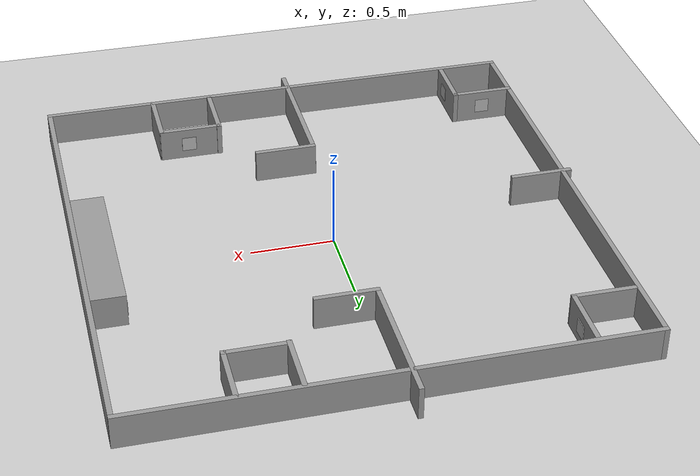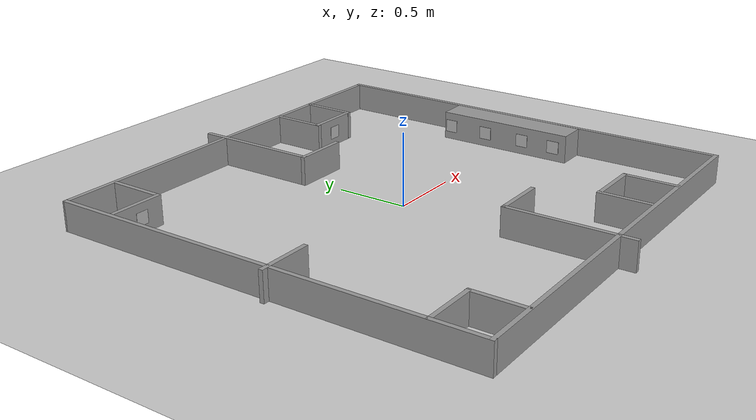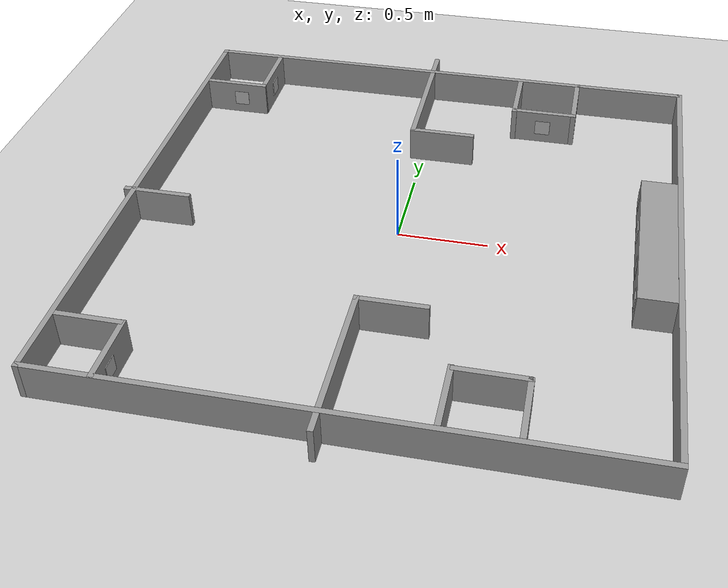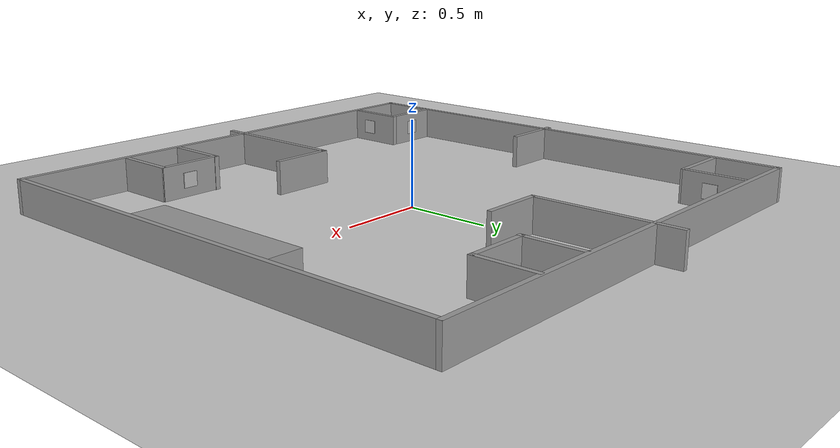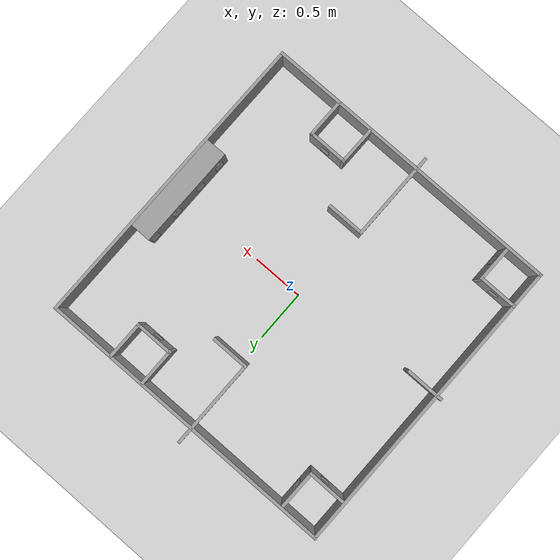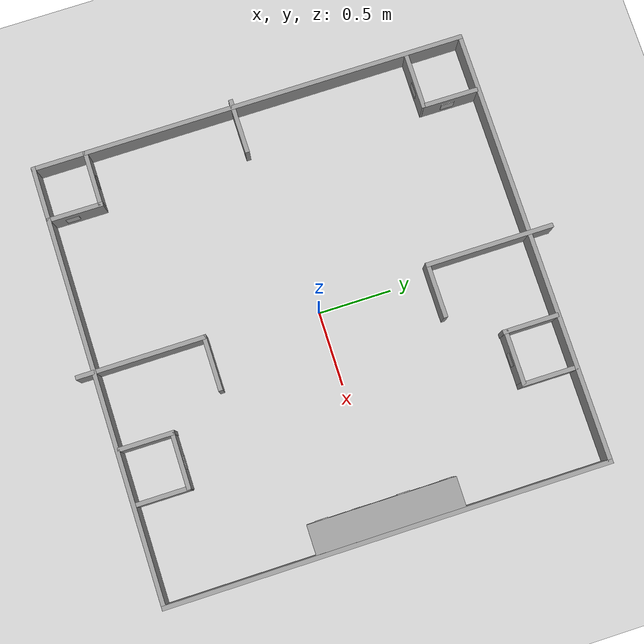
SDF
<sdf version="1.4">
 <world name="default">
  <include><uri>model://sun</uri></include>
  <include><uri>model://ground_plane</uri></include>
  <physics type="ode">
   <real_time_update_rate>1000.0</real_time_update_rate>
   <max_step_size>0.001</max_step_size>
   <real_time_factor>1</real_time_factor>
   <ode>
    <solver>
     <type>quick</type>
     <iters>150</iters>
     <precon_iters>0</precon_iters>
     <sor>1.400000</sor>
     <use_dynamic_moi_rescaling>1</use_dynamic_moi_rescaling>
    </solver>
    <constraints>
     <cfm>0.00001</cfm>
     <erp>0.2</erp>
     <contact_max_correcting_vel>2000.000000</contact_max_correcting_vel>
     <contact_surface_layer>0.01000</contact_surface_layer>
    </constraints>
   </ode>
  </physics>
  <include><pose>0 0 0 0 0 -1.57</pose><uri>model://turtlebot3_home_service/course</uri></include>
  <scene><ambient>0.4 0.4 0.4 1</ambient><background>0.7 0.7 0.7 1</background><shadows>true</shadows></scene>
 </world>
</sdf>

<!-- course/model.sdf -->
<sdf version='1.6'>
  <model name='course'>
    <link name='Wall_11'>
      <pose frame=''>-0.764031 0.114894 0 0 0 -1.5708</pose>
      <self_collide>0</self_collide>
      <kinematic>0</kinematic>
      <visual name='Wall_11_Visual'>
        <pose frame=''>0 0 0.1 0 -0 0</pose>
        <geometry>
          <box>
            <size>0.380343 0.03 0.2</size>
          </box>
        </geometry>
        <material>
          <script>
            <uri>file://media/materials/scripts/gazebo.material</uri>
            <name>Gazebo/Grey</name>
          </script>
          <ambient>1 1 1 1</ambient>
          <diffuse>0.7 0.7 0.7 1</diffuse>
          <specular>0.01 0.01 0.01 1</specular>
          <emissive>0 0 0 1</emissive>
        </material>
        <cast_shadows>1</cast_shadows>
        <transparency>0</transparency>
      </visual>
      <collision name='Wall_11_Collision'>
        <laser_retro>0</laser_retro>
        <max_contacts>10</max_contacts>
        <pose frame=''>0 0 0.1 0 -0 0</pose>
        <geometry>
          <box>
            <size>0.380343 0.03 0.2</size>
          </box>
        </geometry>
        <surface>
          <friction>
            <ode>
              <mu>1</mu>
              <mu2>1</mu2>
              <fdir1>0 0 0</fdir1>
              <slip1>0</slip1>
              <slip2>0</slip2>
            </ode>
            <torsional>
              <coefficient>1</coefficient>
              <patch_radius>0</patch_radius>
              <surface_radius>0</surface_radius>
              <use_patch_radius>1</use_patch_radius>
              <ode>
                <slip>0</slip>
              </ode>
            </torsional>
          </friction>
          <bounce>
            <restitution_coefficient>0</restitution_coefficient>
            <threshold>1e+06</threshold>
          </bounce>
          <contact>
            <collide_without_contact>0</collide_without_contact>
            <collide_without_contact_bitmask>1</collide_without_contact_bitmask>
            <collide_bitmask>1</collide_bitmask>
            <ode>
              <soft_cfm>0</soft_cfm>
              <soft_erp>0.2</soft_erp>
              <kp>1e+13</kp>
              <kd>1</kd>
              <max_vel>0.01</max_vel>
              <min_depth>0</min_depth>
            </ode>
            <bullet>
              <split_impulse>1</split_impulse>
              <split_impulse_penetration_threshold>-0.01</split_impulse_penetration_threshold>
              <soft_cfm>0</soft_cfm>
              <soft_erp>0.2</soft_erp>
              <kp>1e+13</kp>
              <kd>1</kd>
            </bullet>
          </contact>
        </surface>
      </collision>
    </link>
    <link name='Wall_11_clone'>
      <pose frame=''>-1.27339 0.511234 0 0 0 -0.0008</pose>
      <self_collide>0</self_collide>
      <kinematic>0</kinematic>
      <visual name='Wall_11_Visual'>
        <pose frame=''>0 0 0.1 0 -0 0</pose>
        <geometry>
          <box>
            <size>0.380343 0.03 0.2</size>
          </box>
        </geometry>
        <material>
          <script>
            <uri>file://media/materials/scripts/gazebo.material</uri>
            <name>Gazebo/Grey</name>
          </script>
          <ambient>1 1 1 1</ambient>
          <diffuse>0.7 0.7 0.7 1</diffuse>
          <specular>0.01 0.01 0.01 1</specular>
          <emissive>0 0 0 1</emissive>
          <shader type='pixel'/>
        </material>
        <cast_shadows>1</cast_shadows>
        <transparency>0</transparency>
      </visual>
      <collision name='Wall_11_Collision'>
        <laser_retro>0</laser_retro>
        <max_contacts>10</max_contacts>
        <pose frame=''>0 0 0.1 0 -0 0</pose>
        <geometry>
          <box>
            <size>0.380343 0.03 0.2</size>
          </box>
        </geometry>
        <surface>
          <friction>
            <ode>
              <mu>1</mu>
              <mu2>1</mu2>
              <fdir1>0 0 0</fdir1>
              <slip1>0</slip1>
              <slip2>0</slip2>
            </ode>
            <torsional>
              <coefficient>1</coefficient>
              <patch_radius>0</patch_radius>
              <surface_radius>0</surface_radius>
              <use_patch_radius>1</use_patch_radius>
              <ode>
                <slip>0</slip>
              </ode>
            </torsional>
          </friction>
          <bounce>
            <restitution_coefficient>0</restitution_coefficient>
            <threshold>1e+06</threshold>
          </bounce>
          <contact>
            <collide_without_contact>0</collide_without_contact>
            <collide_without_contact_bitmask>1</collide_without_contact_bitmask>
            <collide_bitmask>1</collide_bitmask>
            <ode>
              <soft_cfm>0</soft_cfm>
              <soft_erp>0.2</soft_erp>
              <kp>1e+13</kp>
              <kd>1</kd>
              <max_vel>0.01</max_vel>
              <min_depth>0</min_depth>
            </ode>
            <bullet>
              <split_impulse>1</split_impulse>
              <split_impulse_penetration_threshold>-0.01</split_impulse_penetration_threshold>
              <soft_cfm>0</soft_cfm>
              <soft_erp>0.2</soft_erp>
              <kp>1e+13</kp>
              <kd>1</kd>
            </bullet>
          </contact>
        </surface>
      </collision>
    </link>
    <link name='Wall_11_clone_clone'>
      <pose frame=''>-1.10256 0.692997 0 0 -0 1.5692</pose>
      <self_collide>0</self_collide>
      <kinematic>0</kinematic>
      <visual name='Wall_11_Visual'>
        <pose frame=''>0 0 0.1 0 -0 0</pose>
        <geometry>
          <box>
            <size>0.380343 0.03 0.2</size>
          </box>
        </geometry>
        <material>
          <script>
            <uri>file://media/materials/scripts/gazebo.material</uri>
            <name>Gazebo/Grey</name>
          </script>
          <ambient>1 1 1 1</ambient>
          <diffuse>0.7 0.7 0.7 1</diffuse>
          <specular>0.01 0.01 0.01 1</specular>
          <emissive>0 0 0 1</emissive>
          <shader type='pixel'/>
        </material>
        <cast_shadows>1</cast_shadows>
        <transparency>0</transparency>
      </visual>
      <collision name='Wall_11_Collision'>
        <laser_retro>0</laser_retro>
        <max_contacts>10</max_contacts>
        <pose frame=''>0 0 0.1 0 -0 0</pose>
        <geometry>
          <box>
            <size>0.380343 0.03 0.2</size>
          </box>
        </geometry>
        <surface>
          <friction>
            <ode>
              <mu>1</mu>
              <mu2>1</mu2>
              <fdir1>0 0 0</fdir1>
              <slip1>0</slip1>
              <slip2>0</slip2>
            </ode>
            <torsional>
              <coefficient>1</coefficient>
              <patch_radius>0</patch_radius>
              <surface_radius>0</surface_radius>
              <use_patch_radius>1</use_patch_radius>
              <ode>
                <slip>0</slip>
              </ode>
            </torsional>
          </friction>
          <bounce>
            <restitution_coefficient>0</restitution_coefficient>
            <threshold>1e+06</threshold>
          </bounce>
          <contact>
            <collide_without_contact>0</collide_without_contact>
            <collide_without_contact_bitmask>1</collide_without_contact_bitmask>
            <collide_bitmask>1</collide_bitmask>
            <ode>
              <soft_cfm>0</soft_cfm>
              <soft_erp>0.2</soft_erp>
              <kp>1e+13</kp>
              <kd>1</kd>
              <max_vel>0.01</max_vel>
              <min_depth>0</min_depth>
            </ode>
            <bullet>
              <split_impulse>1</split_impulse>
              <split_impulse_penetration_threshold>-0.01</split_impulse_penetration_threshold>
              <soft_cfm>0</soft_cfm>
              <soft_erp>0.2</soft_erp>
              <kp>1e+13</kp>
              <kd>1</kd>
            </bullet>
          </contact>
        </surface>
      </collision>
    </link>
    <link name='Wall_11_clone_clone_clone'>
      <pose frame=''>-1.27687 0.869348 0 0 -0 3.1392</pose>
      <self_collide>0</self_collide>
      <kinematic>0</kinematic>
      <visual name='Wall_11_Visual'>
        <pose frame=''>0 0 0.1 0 -0 0</pose>
        <geometry>
          <box>
            <size>0.380343 0.03 0.2</size>
          </box>
        </geometry>
        <material>
          <script>
            <uri>file://media/materials/scripts/gazebo.material</uri>
            <name>Gazebo/Grey</name>
          </script>
          <ambient>1 1 1 1</ambient>
          <diffuse>0.7 0.7 0.7 1</diffuse>
          <specular>0.01 0.01 0.01 1</specular>
          <emissive>0 0 0 1</emissive>
          <shader type='pixel'/>
        </material>
        <cast_shadows>1</cast_shadows>
        <transparency>0</transparency>
      </visual>
      <collision name='Wall_11_Collision'>
        <laser_retro>0</laser_retro>
        <max_contacts>10</max_contacts>
        <pose frame=''>0 0 0.1 0 -0 0</pose>
        <geometry>
          <box>
            <size>0.380343 0.03 0.2</size>
          </box>
        </geometry>
        <surface>
          <friction>
            <ode>
              <mu>1</mu>
              <mu2>1</mu2>
              <fdir1>0 0 0</fdir1>
              <slip1>0</slip1>
              <slip2>0</slip2>
            </ode>
            <torsional>
              <coefficient>1</coefficient>
              <patch_radius>0</patch_radius>
              <surface_radius>0</surface_radius>
              <use_patch_radius>1</use_patch_radius>
              <ode>
                <slip>0</slip>
              </ode>
            </torsional>
          </friction>
          <bounce>
            <restitution_coefficient>0</restitution_coefficient>
            <threshold>1e+06</threshold>
          </bounce>
          <contact>
            <collide_without_contact>0</collide_without_contact>
            <collide_without_contact_bitmask>1</collide_without_contact_bitmask>
            <collide_bitmask>1</collide_bitmask>
            <ode>
              <soft_cfm>0</soft_cfm>
              <soft_erp>0.2</soft_erp>
              <kp>1e+13</kp>
              <kd>1</kd>
              <max_vel>0.01</max_vel>
              <min_depth>0</min_depth>
            </ode>
            <bullet>
              <split_impulse>1</split_impulse>
              <split_impulse_penetration_threshold>-0.01</split_impulse_penetration_threshold>
              <soft_cfm>0</soft_cfm>
              <soft_erp>0.2</soft_erp>
              <kp>1e+13</kp>
              <kd>1</kd>
            </bullet>
          </contact>
        </surface>
      </collision>
    </link>
    <link name='Wall_11_clone_clone_clone_0'>
      <pose frame=''>1.32098 0.840435 0 0 -0 3.1392</pose>
      <self_collide>0</self_collide>
      <kinematic>0</kinematic>
      <visual name='Wall_11_Visual'>
        <pose frame=''>0 0 0.1 0 -0 0</pose>
        <geometry>
          <box>
            <size>0.380343 0.03 0.2</size>
          </box>
        </geometry>
        <material>
          <script>
            <uri>file://media/materials/scripts/gazebo.material</uri>
            <name>Gazebo/Grey</name>
          </script>
          <ambient>1 1 1 1</ambient>
          <diffuse>0.7 0.7 0.7 1</diffuse>
          <specular>0.01 0.01 0.01 1</specular>
          <emissive>0 0 0 1</emissive>
          <shader type='pixel'/>
        </material>
        <cast_shadows>1</cast_shadows>
        <transparency>0</transparency>
      </visual>
      <collision name='Wall_11_Collision'>
        <laser_retro>0</laser_retro>
        <max_contacts>10</max_contacts>
        <pose frame=''>0 0 0.1 0 -0 0</pose>
        <geometry>
          <box>
            <size>0.380343 0.03 0.2</size>
          </box>
        </geometry>
        <surface>
          <friction>
            <ode>
              <mu>1</mu>
              <mu2>1</mu2>
              <fdir1>0 0 0</fdir1>
              <slip1>0</slip1>
              <slip2>0</slip2>
            </ode>
            <torsional>
              <coefficient>1</coefficient>
              <patch_radius>0</patch_radius>
              <surface_radius>0</surface_radius>
              <use_patch_radius>1</use_patch_radius>
              <ode>
                <slip>0</slip>
              </ode>
            </torsional>
          </friction>
          <bounce>
            <restitution_coefficient>0</restitution_coefficient>
            <threshold>1e+06</threshold>
          </bounce>
          <contact>
            <collide_without_contact>0</collide_without_contact>
            <collide_without_contact_bitmask>1</collide_without_contact_bitmask>
            <collide_bitmask>1</collide_bitmask>
            <ode>
              <soft_cfm>0</soft_cfm>
              <soft_erp>0.2</soft_erp>
              <kp>1e+13</kp>
              <kd>1</kd>
              <max_vel>0.01</max_vel>
              <min_depth>0</min_depth>
            </ode>
            <bullet>
              <split_impulse>1</split_impulse>
              <split_impulse_penetration_threshold>-0.01</split_impulse_penetration_threshold>
              <soft_cfm>0</soft_cfm>
              <soft_erp>0.2</soft_erp>
              <kp>1e+13</kp>
              <kd>1</kd>
            </bullet>
          </contact>
        </surface>
      </collision>
    </link>
    <link name='Wall_11_clone_clone_clone_clone'>
      <pose frame=''>1.14091 0.66035 0 0 0 -1.57398</pose>
      <self_collide>0</self_collide>
      <kinematic>0</kinematic>
      <visual name='Wall_11_Visual'>
        <pose frame=''>0 0 0.1 0 -0 0</pose>
        <geometry>
          <box>
            <size>0.380343 0.03 0.2</size>
          </box>
        </geometry>
        <material>
          <script>
            <uri>file://media/materials/scripts/gazebo.material</uri>
            <name>Gazebo/Grey</name>
          </script>
          <ambient>1 1 1 1</ambient>
          <diffuse>0.7 0.7 0.7 1</diffuse>
          <specular>0.01 0.01 0.01 1</specular>
          <emissive>0 0 0 1</emissive>
          <shader type='pixel'/>
        </material>
        <cast_shadows>1</cast_shadows>
        <transparency>0</transparency>
      </visual>
      <collision name='Wall_11_Collision'>
        <laser_retro>0</laser_retro>
        <max_contacts>10</max_contacts>
        <pose frame=''>0 0 0.1 0 -0 0</pose>
        <geometry>
          <box>
            <size>0.380343 0.03 0.2</size>
          </box>
        </geometry>
        <surface>
          <friction>
            <ode>
              <mu>1</mu>
              <mu2>1</mu2>
              <fdir1>0 0 0</fdir1>
              <slip1>0</slip1>
              <slip2>0</slip2>
            </ode>
            <torsional>
              <coefficient>1</coefficient>
              <patch_radius>0</patch_radius>
              <surface_radius>0</surface_radius>
              <use_patch_radius>1</use_patch_radius>
              <ode>
                <slip>0</slip>
              </ode>
            </torsional>
          </friction>
          <bounce>
            <restitution_coefficient>0</restitution_coefficient>
            <threshold>1e+06</threshold>
          </bounce>
          <contact>
            <collide_without_contact>0</collide_without_contact>
            <collide_without_contact_bitmask>1</collide_without_contact_bitmask>
            <collide_bitmask>1</collide_bitmask>
            <ode>
              <soft_cfm>0</soft_cfm>
              <soft_erp>0.2</soft_erp>
              <kp>1e+13</kp>
              <kd>1</kd>
              <max_vel>0.01</max_vel>
              <min_depth>0</min_depth>
            </ode>
            <bullet>
              <split_impulse>1</split_impulse>
              <split_impulse_penetration_threshold>-0.01</split_impulse_penetration_threshold>
              <soft_cfm>0</soft_cfm>
              <soft_erp>0.2</soft_erp>
              <kp>1e+13</kp>
              <kd>1</kd>
            </bullet>
          </contact>
        </surface>
      </collision>
    </link>
    <link name='Wall_11_clone_clone_clone_clone_clone'>
      <pose frame=''>1.31241 0.473395 0 0 0 -0.00398</pose>
      <self_collide>0</self_collide>
      <kinematic>0</kinematic>
      <visual name='Wall_11_Visual'>
        <pose frame=''>0 0 0.1 0 -0 0</pose>
        <geometry>
          <box>
            <size>0.380343 0.03 0.2</size>
          </box>
        </geometry>
        <material>
          <script>
            <uri>file://media/materials/scripts/gazebo.material</uri>
            <name>Gazebo/Grey</name>
          </script>
          <ambient>1 1 1 1</ambient>
          <diffuse>0.7 0.7 0.7 1</diffuse>
          <specular>0.01 0.01 0.01 1</specular>
          <emissive>0 0 0 1</emissive>
          <shader type='pixel'/>
        </material>
        <cast_shadows>1</cast_shadows>
        <transparency>0</transparency>
      </visual>
      <collision name='Wall_11_Collision'>
        <laser_retro>0</laser_retro>
        <max_contacts>10</max_contacts>
        <pose frame=''>0 0 0.1 0 -0 0</pose>
        <geometry>
          <box>
            <size>0.380343 0.03 0.2</size>
          </box>
        </geometry>
        <surface>
          <friction>
            <ode>
              <mu>1</mu>
              <mu2>1</mu2>
              <fdir1>0 0 0</fdir1>
              <slip1>0</slip1>
              <slip2>0</slip2>
            </ode>
            <torsional>
              <coefficient>1</coefficient>
              <patch_radius>0</patch_radius>
              <surface_radius>0</surface_radius>
              <use_patch_radius>1</use_patch_radius>
              <ode>
                <slip>0</slip>
              </ode>
            </torsional>
          </friction>
          <bounce>
            <restitution_coefficient>0</restitution_coefficient>
            <threshold>1e+06</threshold>
          </bounce>
          <contact>
            <collide_without_contact>0</collide_without_contact>
            <collide_without_contact_bitmask>1</collide_without_contact_bitmask>
            <collide_bitmask>1</collide_bitmask>
            <ode>
              <soft_cfm>0</soft_cfm>
              <soft_erp>0.2</soft_erp>
              <kp>1e+13</kp>
              <kd>1</kd>
              <max_vel>0.01</max_vel>
              <min_depth>0</min_depth>
            </ode>
            <bullet>
              <split_impulse>1</split_impulse>
              <split_impulse_penetration_threshold>-0.01</split_impulse_penetration_threshold>
              <soft_cfm>0</soft_cfm>
              <soft_erp>0.2</soft_erp>
              <kp>1e+13</kp>
              <kd>1</kd>
            </bullet>
          </contact>
        </surface>
      </collision>
    </link>
    <link name='Wall_11_clone_clone_clone_clone_clone_clone'>
      <pose frame=''>1.15084 -1.2876 0 0 -0 1.56602</pose>
      <self_collide>0</self_collide>
      <kinematic>0</kinematic>
      <visual name='Wall_11_Visual'>
        <pose frame=''>0 0 0.1 0 -0 0</pose>
        <geometry>
          <box>
            <size>0.380343 0.03 0.2</size>
          </box>
        </geometry>
        <material>
          <script>
            <uri>file://media/materials/scripts/gazebo.material</uri>
            <name>Gazebo/Grey</name>
          </script>
          <ambient>1 1 1 1</ambient>
          <diffuse>0.7 0.7 0.7 1</diffuse>
          <specular>0.01 0.01 0.01 1</specular>
          <emissive>0 0 0 1</emissive>
          <shader type='pixel'/>
        </material>
        <cast_shadows>1</cast_shadows>
        <transparency>0</transparency>
      </visual>
      <collision name='Wall_11_Collision'>
        <laser_retro>0</laser_retro>
        <max_contacts>10</max_contacts>
        <pose frame=''>0 0 0.1 0 -0 0</pose>
        <geometry>
          <box>
            <size>0.380343 0.03 0.2</size>
          </box>
        </geometry>
        <surface>
          <friction>
            <ode>
              <mu>1</mu>
              <mu2>1</mu2>
              <fdir1>0 0 0</fdir1>
              <slip1>0</slip1>
              <slip2>0</slip2>
            </ode>
            <torsional>
              <coefficient>1</coefficient>
              <patch_radius>0</patch_radius>
              <surface_radius>0</surface_radius>
              <use_patch_radius>1</use_patch_radius>
              <ode>
                <slip>0</slip>
              </ode>
            </torsional>
          </friction>
          <bounce>
            <restitution_coefficient>0</restitution_coefficient>
            <threshold>1e+06</threshold>
          </bounce>
          <contact>
            <collide_without_contact>0</collide_without_contact>
            <collide_without_contact_bitmask>1</collide_without_contact_bitmask>
            <collide_bitmask>1</collide_bitmask>
            <ode>
              <soft_cfm>0</soft_cfm>
              <soft_erp>0.2</soft_erp>
              <kp>1e+13</kp>
              <kd>1</kd>
              <max_vel>0.01</max_vel>
              <min_depth>0</min_depth>
            </ode>
            <bullet>
              <split_impulse>1</split_impulse>
              <split_impulse_penetration_threshold>-0.01</split_impulse_penetration_threshold>
              <soft_cfm>0</soft_cfm>
              <soft_erp>0.2</soft_erp>
              <kp>1e+13</kp>
              <kd>1</kd>
            </bullet>
          </contact>
        </surface>
      </collision>
    </link>
    <link name='Wall_11_clone_clone_clone_clone_clone_clone_clone'>
      <pose frame=''>1.32573 -1.10236 0 0 -0 3.13602</pose>
      <self_collide>0</self_collide>
      <kinematic>0</kinematic>
      <visual name='Wall_11_Visual'>
        <pose frame=''>0 0 0.1 0 -0 0</pose>
        <geometry>
          <box>
            <size>0.380343 0.03 0.2</size>
          </box>
        </geometry>
        <material>
          <script>
            <uri>file://media/materials/scripts/gazebo.material</uri>
            <name>Gazebo/Grey</name>
          </script>
          <ambient>1 1 1 1</ambient>
          <diffuse>0.7 0.7 0.7 1</diffuse>
          <specular>0.01 0.01 0.01 1</specular>
          <emissive>0 0 0 1</emissive>
          <shader type='pixel'/>
        </material>
        <cast_shadows>1</cast_shadows>
        <transparency>0</transparency>
      </visual>
      <collision name='Wall_11_Collision'>
        <laser_retro>0</laser_retro>
        <max_contacts>10</max_contacts>
        <pose frame=''>0 0 0.1 0 -0 0</pose>
        <geometry>
          <box>
            <size>0.380343 0.03 0.2</size>
          </box>
        </geometry>
        <surface>
          <friction>
            <ode>
              <mu>1</mu>
              <mu2>1</mu2>
              <fdir1>0 0 0</fdir1>
              <slip1>0</slip1>
              <slip2>0</slip2>
            </ode>
            <torsional>
              <coefficient>1</coefficient>
              <patch_radius>0</patch_radius>
              <surface_radius>0</surface_radius>
              <use_patch_radius>1</use_patch_radius>
              <ode>
                <slip>0</slip>
              </ode>
            </torsional>
          </friction>
          <bounce>
            <restitution_coefficient>0</restitution_coefficient>
            <threshold>1e+06</threshold>
          </bounce>
          <contact>
            <collide_without_contact>0</collide_without_contact>
            <collide_without_contact_bitmask>1</collide_without_contact_bitmask>
            <collide_bitmask>1</collide_bitmask>
            <ode>
              <soft_cfm>0</soft_cfm>
              <soft_erp>0.2</soft_erp>
              <kp>1e+13</kp>
              <kd>1</kd>
              <max_vel>0.01</max_vel>
              <min_depth>0</min_depth>
            </ode>
            <bullet>
              <split_impulse>1</split_impulse>
              <split_impulse_penetration_threshold>-0.01</split_impulse_penetration_threshold>
              <soft_cfm>0</soft_cfm>
              <soft_erp>0.2</soft_erp>
              <kp>1e+13</kp>
              <kd>1</kd>
            </bullet>
          </contact>
        </surface>
      </collision>
    </link>
    <link name='Wall_11_clone_clone_clone_clone_clone_clone_clone_clone'>
      <pose frame=''>-1.07993 -1.26306 0 0 0 -1.57716</pose>
      <self_collide>0</self_collide>
      <kinematic>0</kinematic>
      <visual name='Wall_11_Visual'>
        <pose frame=''>0 0 0.1 0 -0 0</pose>
        <geometry>
          <box>
            <size>0.380343 0.03 0.2</size>
          </box>
        </geometry>
        <material>
          <script>
            <uri>file://media/materials/scripts/gazebo.material</uri>
            <name>Gazebo/Grey</name>
          </script>
          <ambient>1 1 1 1</ambient>
          <diffuse>0.7 0.7 0.7 1</diffuse>
          <specular>0.01 0.01 0.01 1</specular>
          <emissive>0 0 0 1</emissive>
          <shader type='pixel'/>
        </material>
        <cast_shadows>1</cast_shadows>
        <transparency>0</transparency>
      </visual>
      <collision name='Wall_11_Collision'>
        <laser_retro>0</laser_retro>
        <max_contacts>10</max_contacts>
        <pose frame=''>0 0 0.1 0 -0 0</pose>
        <geometry>
          <box>
            <size>0.380343 0.03 0.2</size>
          </box>
        </geometry>
        <surface>
          <friction>
            <ode>
              <mu>1</mu>
              <mu2>1</mu2>
              <fdir1>0 0 0</fdir1>
              <slip1>0</slip1>
              <slip2>0</slip2>
            </ode>
            <torsional>
              <coefficient>1</coefficient>
              <patch_radius>0</patch_radius>
              <surface_radius>0</surface_radius>
              <use_patch_radius>1</use_patch_radius>
              <ode>
                <slip>0</slip>
              </ode>
            </torsional>
          </friction>
          <bounce>
            <restitution_coefficient>0</restitution_coefficient>
            <threshold>1e+06</threshold>
          </bounce>
          <contact>
            <collide_without_contact>0</collide_without_contact>
            <collide_without_contact_bitmask>1</collide_without_contact_bitmask>
            <collide_bitmask>1</collide_bitmask>
            <ode>
              <soft_cfm>0</soft_cfm>
              <soft_erp>0.2</soft_erp>
              <kp>1e+13</kp>
              <kd>1</kd>
              <max_vel>0.01</max_vel>
              <min_depth>0</min_depth>
            </ode>
            <bullet>
              <split_impulse>1</split_impulse>
              <split_impulse_penetration_threshold>-0.01</split_impulse_penetration_threshold>
              <soft_cfm>0</soft_cfm>
              <soft_erp>0.2</soft_erp>
              <kp>1e+13</kp>
              <kd>1</kd>
            </bullet>
          </contact>
        </surface>
      </collision>
    </link>
    <link name='Wall_11_clone_clone_clone_clone_clone_clone_clone_clone_clone'>
      <pose frame=''>-1.26695 -1.08537 0 0 0 -0.00716</pose>
      <self_collide>0</self_collide>
      <kinematic>0</kinematic>
      <visual name='Wall_11_Visual'>
        <pose frame=''>0 0 0.1 0 -0 0</pose>
        <geometry>
          <box>
            <size>0.380343 0.03 0.2</size>
          </box>
        </geometry>
        <material>
          <script>
            <uri>file://media/materials/scripts/gazebo.material</uri>
            <name>Gazebo/Grey</name>
          </script>
          <ambient>1 1 1 1</ambient>
          <diffuse>0.7 0.7 0.7 1</diffuse>
          <specular>0.01 0.01 0.01 1</specular>
          <emissive>0 0 0 1</emissive>
          <shader type='pixel'/>
        </material>
        <cast_shadows>1</cast_shadows>
        <transparency>0</transparency>
      </visual>
      <collision name='Wall_11_Collision'>
        <laser_retro>0</laser_retro>
        <max_contacts>10</max_contacts>
        <pose frame=''>0 0 0.1 0 -0 0</pose>
        <geometry>
          <box>
            <size>0.380343 0.03 0.2</size>
          </box>
        </geometry>
        <surface>
          <friction>
            <ode>
              <mu>1</mu>
              <mu2>1</mu2>
              <fdir1>0 0 0</fdir1>
              <slip1>0</slip1>
              <slip2>0</slip2>
            </ode>
            <torsional>
              <coefficient>1</coefficient>
              <patch_radius>0</patch_radius>
              <surface_radius>0</surface_radius>
              <use_patch_radius>1</use_patch_radius>
              <ode>
                <slip>0</slip>
              </ode>
            </torsional>
          </friction>
          <bounce>
            <restitution_coefficient>0</restitution_coefficient>
            <threshold>1e+06</threshold>
          </bounce>
          <contact>
            <collide_without_contact>0</collide_without_contact>
            <collide_without_contact_bitmask>1</collide_without_contact_bitmask>
            <collide_bitmask>1</collide_bitmask>
            <ode>
              <soft_cfm>0</soft_cfm>
              <soft_erp>0.2</soft_erp>
              <kp>1e+13</kp>
              <kd>1</kd>
              <max_vel>0.01</max_vel>
              <min_depth>0</min_depth>
            </ode>
            <bullet>
              <split_impulse>1</split_impulse>
              <split_impulse_penetration_threshold>-0.01</split_impulse_penetration_threshold>
              <soft_cfm>0</soft_cfm>
              <soft_erp>0.2</soft_erp>
              <kp>1e+13</kp>
              <kd>1</kd>
            </bullet>
          </contact>
        </surface>
      </collision>
    </link>
    <link name='Wall_12'>
      <pose frame=''>-1.18903 -0.060106 0 0 -0 3.14159</pose>
      <self_collide>0</self_collide>
      <kinematic>0</kinematic>
      <visual name='Wall_12_Visual'>
        <pose frame=''>0 0 0.1 0 -0 0</pose>
        <geometry>
          <box>
            <size>0.879643 0.03 0.2</size>
          </box>
        </geometry>
        <material>
          <script>
            <uri>file://media/materials/scripts/gazebo.material</uri>
            <name>Gazebo/Grey</name>
          </script>
          <ambient>1 1 1 1</ambient>
          <diffuse>0.7 0.7 0.7 1</diffuse>
          <specular>0.01 0.01 0.01 1</specular>
          <emissive>0 0 0 1</emissive>
        </material>
        <cast_shadows>1</cast_shadows>
        <transparency>0</transparency>
      </visual>
      <collision name='Wall_12_Collision'>
        <laser_retro>0</laser_retro>
        <max_contacts>10</max_contacts>
        <pose frame=''>0 0 0.1 0 -0 0</pose>
        <geometry>
          <box>
            <size>0.879643 0.03 0.2</size>
          </box>
        </geometry>
        <surface>
          <friction>
            <ode>
              <mu>1</mu>
              <mu2>1</mu2>
              <fdir1>0 0 0</fdir1>
              <slip1>0</slip1>
              <slip2>0</slip2>
            </ode>
            <torsional>
              <coefficient>1</coefficient>
              <patch_radius>0</patch_radius>
              <surface_radius>0</surface_radius>
              <use_patch_radius>1</use_patch_radius>
              <ode>
                <slip>0</slip>
              </ode>
            </torsional>
          </friction>
          <bounce>
            <restitution_coefficient>0</restitution_coefficient>
            <threshold>1e+06</threshold>
          </bounce>
          <contact>
            <collide_without_contact>0</collide_without_contact>
            <collide_without_contact_bitmask>1</collide_without_contact_bitmask>
            <collide_bitmask>1</collide_bitmask>
            <ode>
              <soft_cfm>0</soft_cfm>
              <soft_erp>0.2</soft_erp>
              <kp>1e+13</kp>
              <kd>1</kd>
              <max_vel>0.01</max_vel>
              <min_depth>0</min_depth>
            </ode>
            <bullet>
              <split_impulse>1</split_impulse>
              <split_impulse_penetration_threshold>-0.01</split_impulse_penetration_threshold>
              <soft_cfm>0</soft_cfm>
              <soft_erp>0.2</soft_erp>
              <kp>1e+13</kp>
              <kd>1</kd>
            </bullet>
          </contact>
        </surface>
      </collision>
    </link>
    <link name='Wall_14'>
      <pose frame=''>0.763969 0.121894 0 0 0 -1.5708</pose>
      <self_collide>0</self_collide>
      <kinematic>0</kinematic>
      <visual name='Wall_14_Visual'>
        <pose frame=''>0 0 0.1 0 -0 0</pose>
        <geometry>
          <box>
            <size>0.379782 0.03 0.2</size>
          </box>
        </geometry>
        <material>
          <script>
            <uri>file://media/materials/scripts/gazebo.material</uri>
            <name>Gazebo/Grey</name>
          </script>
          <ambient>1 1 1 1</ambient>
          <diffuse>0.7 0.7 0.7 1</diffuse>
          <specular>0.01 0.01 0.01 1</specular>
          <emissive>0 0 0 1</emissive>
        </material>
        <cast_shadows>1</cast_shadows>
        <transparency>0</transparency>
      </visual>
      <collision name='Wall_14_Collision'>
        <laser_retro>0</laser_retro>
        <max_contacts>10</max_contacts>
        <pose frame=''>0 0 0.1 0 -0 0</pose>
        <geometry>
          <box>
            <size>0.379782 0.03 0.2</size>
          </box>
        </geometry>
        <surface>
          <friction>
            <ode>
              <mu>1</mu>
              <mu2>1</mu2>
              <fdir1>0 0 0</fdir1>
              <slip1>0</slip1>
              <slip2>0</slip2>
            </ode>
            <torsional>
              <coefficient>1</coefficient>
              <patch_radius>0</patch_radius>
              <surface_radius>0</surface_radius>
              <use_patch_radius>1</use_patch_radius>
              <ode>
                <slip>0</slip>
              </ode>
            </torsional>
          </friction>
          <bounce>
            <restitution_coefficient>0</restitution_coefficient>
            <threshold>1e+06</threshold>
          </bounce>
          <contact>
            <collide_without_contact>0</collide_without_contact>
            <collide_without_contact_bitmask>1</collide_without_contact_bitmask>
            <collide_bitmask>1</collide_bitmask>
            <ode>
              <soft_cfm>0</soft_cfm>
              <soft_erp>0.2</soft_erp>
              <kp>1e+13</kp>
              <kd>1</kd>
              <max_vel>0.01</max_vel>
              <min_depth>0</min_depth>
            </ode>
            <bullet>
              <split_impulse>1</split_impulse>
              <split_impulse_penetration_threshold>-0.01</split_impulse_penetration_threshold>
              <soft_cfm>0</soft_cfm>
              <soft_erp>0.2</soft_erp>
              <kp>1e+13</kp>
              <kd>1</kd>
            </bullet>
          </contact>
        </surface>
      </collision>
    </link>
    <link name='Wall_15'>
      <pose frame=''>1.18897 -0.053106 0 0 -0 0</pose>
      <self_collide>0</self_collide>
      <kinematic>0</kinematic>
      <visual name='Wall_15_Visual'>
        <pose frame=''>0 0 0.1 0 -0 0</pose>
        <geometry>
          <box>
            <size>0.879767 0.03 0.2</size>
          </box>
        </geometry>
        <material>
          <script>
            <uri>file://media/materials/scripts/gazebo.material</uri>
            <name>Gazebo/Grey</name>
          </script>
          <ambient>1 1 1 1</ambient>
          <diffuse>0.7 0.7 0.7 1</diffuse>
          <specular>0.01 0.01 0.01 1</specular>
          <emissive>0 0 0 1</emissive>
        </material>
        <cast_shadows>1</cast_shadows>
        <transparency>0</transparency>
      </visual>
      <collision name='Wall_15_Collision'>
        <laser_retro>0</laser_retro>
        <max_contacts>10</max_contacts>
        <pose frame=''>0 0 0.1 0 -0 0</pose>
        <geometry>
          <box>
            <size>0.879767 0.03 0.2</size>
          </box>
        </geometry>
        <surface>
          <friction>
            <ode>
              <mu>1</mu>
              <mu2>1</mu2>
              <fdir1>0 0 0</fdir1>
              <slip1>0</slip1>
              <slip2>0</slip2>
            </ode>
            <torsional>
              <coefficient>1</coefficient>
              <patch_radius>0</patch_radius>
              <surface_radius>0</surface_radius>
              <use_patch_radius>1</use_patch_radius>
              <ode>
                <slip>0</slip>
              </ode>
            </torsional>
          </friction>
          <bounce>
            <restitution_coefficient>0</restitution_coefficient>
            <threshold>1e+06</threshold>
          </bounce>
          <contact>
            <collide_without_contact>0</collide_without_contact>
            <collide_without_contact_bitmask>1</collide_without_contact_bitmask>
            <collide_bitmask>1</collide_bitmask>
            <ode>
              <soft_cfm>0</soft_cfm>
              <soft_erp>0.2</soft_erp>
              <kp>1e+13</kp>
              <kd>1</kd>
              <max_vel>0.01</max_vel>
              <min_depth>0</min_depth>
            </ode>
            <bullet>
              <split_impulse>1</split_impulse>
              <split_impulse_penetration_threshold>-0.01</split_impulse_penetration_threshold>
              <soft_cfm>0</soft_cfm>
              <soft_erp>0.2</soft_erp>
              <kp>1e+13</kp>
              <kd>1</kd>
            </bullet>
          </contact>
        </surface>
      </collision>
    </link>
    <link name='Wall_17'>
      <pose frame=''>0.128969 -1.33011 0 0 0 -1.5708</pose>
      <self_collide>0</self_collide>
      <kinematic>0</kinematic>
      <visual name='Wall_17_Visual'>
        <pose frame=''>0 0 0.1 0 -0 0</pose>
        <geometry>
          <box>
            <size>0.379578 0.03 0.2</size>
          </box>
        </geometry>
        <material>
          <script>
            <uri>file://media/materials/scripts/gazebo.material</uri>
            <name>Gazebo/Grey</name>
          </script>
          <ambient>1 1 1 1</ambient>
          <diffuse>0.7 0.7 0.7 1</diffuse>
          <specular>0.01 0.01 0.01 1</specular>
          <emissive>0 0 0 1</emissive>
        </material>
        <cast_shadows>1</cast_shadows>
        <transparency>0</transparency>
      </visual>
      <collision name='Wall_17_Collision'>
        <laser_retro>0</laser_retro>
        <max_contacts>10</max_contacts>
        <pose frame=''>0 0 0.1 0 -0 0</pose>
        <geometry>
          <box>
            <size>0.379578 0.03 0.2</size>
          </box>
        </geometry>
        <surface>
          <friction>
            <ode>
              <mu>1</mu>
              <mu2>1</mu2>
              <fdir1>0 0 0</fdir1>
              <slip1>0</slip1>
              <slip2>0</slip2>
            </ode>
            <torsional>
              <coefficient>1</coefficient>
              <patch_radius>0</patch_radius>
              <surface_radius>0</surface_radius>
              <use_patch_radius>1</use_patch_radius>
              <ode>
                <slip>0</slip>
              </ode>
            </torsional>
          </friction>
          <bounce>
            <restitution_coefficient>0</restitution_coefficient>
            <threshold>1e+06</threshold>
          </bounce>
          <contact>
            <collide_without_contact>0</collide_without_contact>
            <collide_without_contact_bitmask>1</collide_without_contact_bitmask>
            <collide_bitmask>1</collide_bitmask>
            <ode>
              <soft_cfm>0</soft_cfm>
              <soft_erp>0.2</soft_erp>
              <kp>1e+13</kp>
              <kd>1</kd>
              <max_vel>0.01</max_vel>
              <min_depth>0</min_depth>
            </ode>
            <bullet>
              <split_impulse>1</split_impulse>
              <split_impulse_penetration_threshold>-0.01</split_impulse_penetration_threshold>
              <soft_cfm>0</soft_cfm>
              <soft_erp>0.2</soft_erp>
              <kp>1e+13</kp>
              <kd>1</kd>
            </bullet>
          </contact>
        </surface>
      </collision>
    </link>
    <link name='Wall_2'>
      <pose frame=''>1.50597 0.019894 0 0 0 -1.5708</pose>
      <self_collide>0</self_collide>
      <kinematic>0</kinematic>
      <visual name='Wall_2_Visual'>
        <pose frame=''>0 0 0.1 0 -0 0</pose>
        <geometry>
          <box>
            <size>3 0.03 0.2</size>
          </box>
        </geometry>
        <material>
          <script>
            <uri>file://media/materials/scripts/gazebo.material</uri>
            <name>Gazebo/Grey</name>
          </script>
          <ambient>1 1 1 1</ambient>
          <diffuse>0.7 0.7 0.7 1</diffuse>
          <specular>0.01 0.01 0.01 1</specular>
          <emissive>0 0 0 1</emissive>
        </material>
        <cast_shadows>1</cast_shadows>
        <transparency>0</transparency>
      </visual>
      <collision name='Wall_2_Collision'>
        <laser_retro>0</laser_retro>
        <max_contacts>10</max_contacts>
        <pose frame=''>0 0 0.1 0 -0 0</pose>
        <geometry>
          <box>
            <size>3 0.03 0.2</size>
          </box>
        </geometry>
        <surface>
          <friction>
            <ode>
              <mu>1</mu>
              <mu2>1</mu2>
              <fdir1>0 0 0</fdir1>
              <slip1>0</slip1>
              <slip2>0</slip2>
            </ode>
            <torsional>
              <coefficient>1</coefficient>
              <patch_radius>0</patch_radius>
              <surface_radius>0</surface_radius>
              <use_patch_radius>1</use_patch_radius>
              <ode>
                <slip>0</slip>
              </ode>
            </torsional>
          </friction>
          <bounce>
            <restitution_coefficient>0</restitution_coefficient>
            <threshold>1e+06</threshold>
          </bounce>
          <contact>
            <collide_without_contact>0</collide_without_contact>
            <collide_without_contact_bitmask>1</collide_without_contact_bitmask>
            <collide_bitmask>1</collide_bitmask>
            <ode>
              <soft_cfm>0</soft_cfm>
              <soft_erp>0.2</soft_erp>
              <kp>1e+13</kp>
              <kd>1</kd>
              <max_vel>0.01</max_vel>
              <min_depth>0</min_depth>
            </ode>
            <bullet>
              <split_impulse>1</split_impulse>
              <split_impulse_penetration_threshold>-0.01</split_impulse_penetration_threshold>
              <soft_cfm>0</soft_cfm>
              <soft_erp>0.2</soft_erp>
              <kp>1e+13</kp>
              <kd>1</kd>
            </bullet>
          </contact>
        </surface>
      </collision>
    </link>
    <link name='Wall_4'>
      <pose frame=''>0.020969 -1.46511 0 0 -0 3.14159</pose>
      <self_collide>0</self_collide>
      <kinematic>0</kinematic>
      <visual name='Wall_4_Visual'>
        <pose frame=''>0 0 0.1 0 -0 0</pose>
        <geometry>
          <box>
            <size>3 0.03 0.2</size>
          </box>
        </geometry>
        <material>
          <script>
            <uri>file://media/materials/scripts/gazebo.material</uri>
            <name>Gazebo/Grey</name>
          </script>
          <ambient>1 1 1 1</ambient>
          <diffuse>0.7 0.7 0.7 1</diffuse>
          <specular>0.01 0.01 0.01 1</specular>
          <emissive>0 0 0 1</emissive>
        </material>
        <cast_shadows>1</cast_shadows>
        <transparency>0</transparency>
      </visual>
      <collision name='Wall_4_Collision'>
        <laser_retro>0</laser_retro>
        <max_contacts>10</max_contacts>
        <pose frame=''>0 0 0.1 0 -0 0</pose>
        <geometry>
          <box>
            <size>3 0.03 0.2</size>
          </box>
        </geometry>
        <surface>
          <friction>
            <ode>
              <mu>1</mu>
              <mu2>1</mu2>
              <fdir1>0 0 0</fdir1>
              <slip1>0</slip1>
              <slip2>0</slip2>
            </ode>
            <torsional>
              <coefficient>1</coefficient>
              <patch_radius>0</patch_radius>
              <surface_radius>0</surface_radius>
              <use_patch_radius>1</use_patch_radius>
              <ode>
                <slip>0</slip>
              </ode>
            </torsional>
          </friction>
          <bounce>
            <restitution_coefficient>0</restitution_coefficient>
            <threshold>1e+06</threshold>
          </bounce>
          <contact>
            <collide_without_contact>0</collide_without_contact>
            <collide_without_contact_bitmask>1</collide_without_contact_bitmask>
            <collide_bitmask>1</collide_bitmask>
            <ode>
              <soft_cfm>0</soft_cfm>
              <soft_erp>0.2</soft_erp>
              <kp>1e+13</kp>
              <kd>1</kd>
              <max_vel>0.01</max_vel>
              <min_depth>0</min_depth>
            </ode>
            <bullet>
              <split_impulse>1</split_impulse>
              <split_impulse_penetration_threshold>-0.01</split_impulse_penetration_threshold>
              <soft_cfm>0</soft_cfm>
              <soft_erp>0.2</soft_erp>
              <kp>1e+13</kp>
              <kd>1</kd>
            </bullet>
          </contact>
        </surface>
      </collision>
    </link>
    <link name='Wall_7'>
      <pose frame=''>-1.46403 0.019894 0 0 -0 1.5708</pose>
      <self_collide>0</self_collide>
      <kinematic>0</kinematic>
      <visual name='Wall_7_Visual'>
        <pose frame=''>0 0 0.1 0 -0 0</pose>
        <geometry>
          <box>
            <size>3 0.03 0.2</size>
          </box>
        </geometry>
        <material>
          <script>
            <uri>file://media/materials/scripts/gazebo.material</uri>
            <name>Gazebo/Grey</name>
          </script>
          <ambient>1 1 1 1</ambient>
          <diffuse>0.7 0.7 0.7 1</diffuse>
          <specular>0.01 0.01 0.01 1</specular>
          <emissive>0 0 0 1</emissive>
        </material>
        <cast_shadows>1</cast_shadows>
        <transparency>0</transparency>
      </visual>
      <collision name='Wall_7_Collision'>
        <laser_retro>0</laser_retro>
        <max_contacts>10</max_contacts>
        <pose frame=''>0 0 0.1 0 -0 0</pose>
        <geometry>
          <box>
            <size>3 0.03 0.2</size>
          </box>
        </geometry>
        <surface>
          <friction>
            <ode>
              <mu>1</mu>
              <mu2>1</mu2>
              <fdir1>0 0 0</fdir1>
              <slip1>0</slip1>
              <slip2>0</slip2>
            </ode>
            <torsional>
              <coefficient>1</coefficient>
              <patch_radius>0</patch_radius>
              <surface_radius>0</surface_radius>
              <use_patch_radius>1</use_patch_radius>
              <ode>
                <slip>0</slip>
              </ode>
            </torsional>
          </friction>
          <bounce>
            <restitution_coefficient>0</restitution_coefficient>
            <threshold>1e+06</threshold>
          </bounce>
          <contact>
            <collide_without_contact>0</collide_without_contact>
            <collide_without_contact_bitmask>1</collide_without_contact_bitmask>
            <collide_bitmask>1</collide_bitmask>
            <ode>
              <soft_cfm>0</soft_cfm>
              <soft_erp>0.2</soft_erp>
              <kp>1e+13</kp>
              <kd>1</kd>
              <max_vel>0.01</max_vel>
              <min_depth>0</min_depth>
            </ode>
            <bullet>
              <split_impulse>1</split_impulse>
              <split_impulse_penetration_threshold>-0.01</split_impulse_penetration_threshold>
              <soft_cfm>0</soft_cfm>
              <soft_erp>0.2</soft_erp>
              <kp>1e+13</kp>
              <kd>1</kd>
            </bullet>
          </contact>
        </surface>
      </collision>
    </link>
    <link name='Wall_9'>
      <pose frame=''>0.020969 1.50489 0 0 -0 0</pose>
      <self_collide>0</self_collide>
      <kinematic>0</kinematic>
      <visual name='Wall_9_Visual'>
        <pose frame=''>0 0 0.1 0 -0 0</pose>
        <geometry>
          <box>
            <size>2.99951 0.03 0.2</size>
          </box>
        </geometry>
        <material>
          <script>
            <uri>file://media/materials/scripts/gazebo.material</uri>
            <name>Gazebo/Grey</name>
          </script>
          <ambient>1 1 1 1</ambient>
          <diffuse>0.7 0.7 0.7 1</diffuse>
          <specular>0.01 0.01 0.01 1</specular>
          <emissive>0 0 0 1</emissive>
        </material>
        <cast_shadows>1</cast_shadows>
        <transparency>0</transparency>
      </visual>
      <collision name='Wall_9_Collision'>
        <laser_retro>0</laser_retro>
        <max_contacts>10</max_contacts>
        <pose frame=''>0 0 0.1 0 -0 0</pose>
        <geometry>
          <box>
            <size>2.99951 0.03 0.2</size>
          </box>
        </geometry>
        <surface>
          <friction>
            <ode>
              <mu>1</mu>
              <mu2>1</mu2>
              <fdir1>0 0 0</fdir1>
              <slip1>0</slip1>
              <slip2>0</slip2>
            </ode>
            <torsional>
              <coefficient>1</coefficient>
              <patch_radius>0</patch_radius>
              <surface_radius>0</surface_radius>
              <use_patch_radius>1</use_patch_radius>
              <ode>
                <slip>0</slip>
              </ode>
            </torsional>
          </friction>
          <bounce>
            <restitution_coefficient>0</restitution_coefficient>
            <threshold>1e+06</threshold>
          </bounce>
          <contact>
            <collide_without_contact>0</collide_without_contact>
            <collide_without_contact_bitmask>1</collide_without_contact_bitmask>
            <collide_bitmask>1</collide_bitmask>
            <ode>
              <soft_cfm>0</soft_cfm>
              <soft_erp>0.2</soft_erp>
              <kp>1e+13</kp>
              <kd>1</kd>
              <max_vel>0.01</max_vel>
              <min_depth>0</min_depth>
            </ode>
            <bullet>
              <split_impulse>1</split_impulse>
              <split_impulse_penetration_threshold>-0.01</split_impulse_penetration_threshold>
              <soft_cfm>0</soft_cfm>
              <soft_erp>0.2</soft_erp>
              <kp>1e+13</kp>
              <kd>1</kd>
            </bullet>
          </contact>
        </surface>
      </collision>
    </link>
    <link name='link_0'>
      <pose frame=''>0.001107 1.39006 0.1 0 -0 1.57</pose>
      <inertial>
        <mass>1</mass>
        <inertia>
          <ixx>0.166667</ixx>
          <ixy>0</ixy>
          <ixz>0</ixz>
          <iyy>0.166667</iyy>
          <iyz>0</iyz>
          <izz>0.166667</izz>
        </inertia>
        <pose frame=''>0 0 0 0 -0 0</pose>
      </inertial>
      <self_collide>0</self_collide>
      <kinematic>0</kinematic>
      <visual name='visual'>
        <pose frame=''>0 0 0 0 -0 0</pose>
        <geometry>
          <box>
            <size>0.2 1 0.2</size>
          </box>
        </geometry>
        <material>
          <lighting>1</lighting>
          <script>
            <uri>file://media/materials/scripts/gazebo.material</uri>
            <name>Gazebo/Grey</name>
          </script>
          <ambient>0.3 0.3 0.3 1</ambient>
          <diffuse>0.7 0.7 0.7 1</diffuse>
          <specular>0.01 0.01 0.01 1</specular>
          <emissive>0 0 0 1</emissive>
          <shader type='vertex'>
            <normal_map>__default__</normal_map>
          </shader>
        </material>
        <cast_shadows>1</cast_shadows>
        <transparency>0</transparency>
      </visual>
      <collision name='collision'>
        <laser_retro>0</laser_retro>
        <max_contacts>10</max_contacts>
        <pose frame=''>0 0 0 0 -0 0</pose>
        <geometry>
          <box>
            <size>0.2 1 0.2</size>
          </box>
        </geometry>
        <surface>
          <friction>
            <ode>
              <mu>1</mu>
              <mu2>1</mu2>
              <fdir1>0 0 0</fdir1>
              <slip1>0</slip1>
              <slip2>0</slip2>
            </ode>
            <torsional>
              <coefficient>1</coefficient>
              <patch_radius>0</patch_radius>
              <surface_radius>0</surface_radius>
              <use_patch_radius>1</use_patch_radius>
              <ode>
                <slip>0</slip>
              </ode>
            </torsional>
          </friction>
          <bounce>
            <restitution_coefficient>0</restitution_coefficient>
            <threshold>1e+06</threshold>
          </bounce>
          <contact>
            <collide_without_contact>0</collide_without_contact>
            <collide_without_contact_bitmask>1</collide_without_contact_bitmask>
            <collide_bitmask>1</collide_bitmask>
            <ode>
              <soft_cfm>0</soft_cfm>
              <soft_erp>0.2</soft_erp>
              <kp>1e+13</kp>
              <kd>1</kd>
              <max_vel>0.01</max_vel>
              <min_depth>0</min_depth>
            </ode>
            <bullet>
              <split_impulse>1</split_impulse>
              <split_impulse_penetration_threshold>-0.01</split_impulse_penetration_threshold>
              <soft_cfm>0</soft_cfm>
              <soft_erp>0.2</soft_erp>
              <kp>1e+13</kp>
              <kd>1</kd>
            </bullet>
          </contact>
        </surface>
      </collision>
    </link>
    <model name='armarker00'>
      <link name='link'>
        <pose frame=''>0 0 0.1 0 -0 0</pose>
        <inertial>
          <mass>1</mass>
          <inertia>
            <ixx>0.166667</ixx>
            <ixy>0</ixy>
            <ixz>0</ixz>
            <iyy>0.166667</iyy>
            <iyz>0</iyz>
            <izz>0.166667</izz>
          </inertia>
          <pose frame=''>0 0 0 0 -0 0</pose>
        </inertial>
        <self_collide>0</self_collide>
        <kinematic>0</kinematic>
        <gravity>1</gravity>
        <visual name='visual'>
          <geometry>
            <box>
              <size>0.09 0.01 0.09</size>
            </box>
          </geometry>
          <material>
            <script>
              <uri>model://turtlebot3_home_service/armarker00/materials/scripts</uri>
              <uri>model://turtlebot3_home_service/armarker00/materials/textures</uri>
              <name>armarker00</name>
            </script>
          </material>
          <pose frame=''>0 0 0 0 -0 0</pose>
          <cast_shadows>1</cast_shadows>
          <transparency>0</transparency>
        </visual>
        <collision name='collision'>
          <laser_retro>0</laser_retro>
          <max_contacts>10</max_contacts>
          <pose frame=''>0 0 0 0 -0 0</pose>
          <geometry>
            <box>
              <size>0.09 0.01 0.09</size>
            </box>
          </geometry>
          <surface>
            <friction>
              <ode>
                <mu>1</mu>
                <mu2>1</mu2>
                <fdir1>0 0 0</fdir1>
                <slip1>0</slip1>
                <slip2>0</slip2>
              </ode>
              <torsional>
                <coefficient>1</coefficient>
                <patch_radius>0</patch_radius>
                <surface_radius>0</surface_radius>
                <use_patch_radius>1</use_patch_radius>
                <ode>
                  <slip>0</slip>
                </ode>
              </torsional>
            </friction>
            <bounce>
              <restitution_coefficient>0</restitution_coefficient>
              <threshold>1e+06</threshold>
            </bounce>
            <contact>
              <collide_without_contact>0</collide_without_contact>
              <collide_without_contact_bitmask>1</collide_without_contact_bitmask>
              <collide_bitmask>1</collide_bitmask>
              <ode>
                <soft_cfm>0</soft_cfm>
                <soft_erp>0.2</soft_erp>
                <kp>1e+13</kp>
                <kd>1</kd>
                <max_vel>0.01</max_vel>
                <min_depth>0</min_depth>
              </ode>
              <bullet>
                <split_impulse>1</split_impulse>
                <split_impulse_penetration_threshold>-0.01</split_impulse_penetration_threshold>
                <soft_cfm>0</soft_cfm>
                <soft_erp>0.2</soft_erp>
                <kp>1e+13</kp>
                <kd>1</kd>
              </bullet>
            </contact>
          </surface>
        </collision>
      </link>
      <static>1</static>
      <allow_auto_disable>1</allow_auto_disable>
      <pose frame=''>-0.443295 1.29206 0 0 -0 0</pose>
    </model>
    <model name='armarker01'>
      <link name='link'>
        <pose frame=''>0 0 0.1 0 -0 0</pose>
        <inertial>
          <mass>1</mass>
          <inertia>
            <ixx>0.166667</ixx>
            <ixy>0</ixy>
            <ixz>0</ixz>
            <iyy>0.166667</iyy>
            <iyz>0</iyz>
            <izz>0.166667</izz>
          </inertia>
          <pose frame=''>0 0 0 0 -0 0</pose>
        </inertial>
        <self_collide>0</self_collide>
        <kinematic>0</kinematic>
        <gravity>1</gravity>
        <visual name='visual'>
          <geometry>
            <box>
              <size>0.09 0.01 0.09</size>
            </box>
          </geometry>
          <material>
            <script>
              <uri>model://turtlebot3_home_service/armarker01/materials/scripts</uri>
              <uri>model://turtlebot3_home_service/armarker01/materials/textures</uri>
              <name>armarker01</name>
            </script>
          </material>
          <pose frame=''>0 0 0 0 -0 0</pose>
          <cast_shadows>1</cast_shadows>
          <transparency>0</transparency>
        </visual>
        <collision name='collision'>
          <laser_retro>0</laser_retro>
          <max_contacts>10</max_contacts>
          <pose frame=''>0 0 0 0 -0 0</pose>
          <geometry>
            <box>
              <size>0.09 0.01 0.09</size>
            </box>
          </geometry>
          <surface>
            <friction>
              <ode>
                <mu>1</mu>
                <mu2>1</mu2>
                <fdir1>0 0 0</fdir1>
                <slip1>0</slip1>
                <slip2>0</slip2>
              </ode>
              <torsional>
                <coefficient>1</coefficient>
                <patch_radius>0</patch_radius>
                <surface_radius>0</surface_radius>
                <use_patch_radius>1</use_patch_radius>
                <ode>
                  <slip>0</slip>
                </ode>
              </torsional>
            </friction>
            <bounce>
              <restitution_coefficient>0</restitution_coefficient>
              <threshold>1e+06</threshold>
            </bounce>
            <contact>
              <collide_without_contact>0</collide_without_contact>
              <collide_without_contact_bitmask>1</collide_without_contact_bitmask>
              <collide_bitmask>1</collide_bitmask>
              <ode>
                <soft_cfm>0</soft_cfm>
                <soft_erp>0.2</soft_erp>
                <kp>1e+13</kp>
                <kd>1</kd>
                <max_vel>0.01</max_vel>
                <min_depth>0</min_depth>
              </ode>
              <bullet>
                <split_impulse>1</split_impulse>
                <split_impulse_penetration_threshold>-0.01</split_impulse_penetration_threshold>
                <soft_cfm>0</soft_cfm>
                <soft_erp>0.2</soft_erp>
                <kp>1e+13</kp>
                <kd>1</kd>
              </bullet>
            </contact>
          </surface>
        </collision>
      </link>
      <static>1</static>
      <allow_auto_disable>1</allow_auto_disable>
      <pose frame=''>-0.151432 1.29014 0 0 -0 0</pose>
    </model>
    <model name='armarker02'>
      <link name='link'>
        <pose frame=''>0 0 0.1 0 -0 0</pose>
        <inertial>
          <mass>1</mass>
          <inertia>
            <ixx>0.166667</ixx>
            <ixy>0</ixy>
            <ixz>0</ixz>
            <iyy>0.166667</iyy>
            <iyz>0</iyz>
            <izz>0.166667</izz>
          </inertia>
          <pose frame=''>0 0 0 0 -0 0</pose>
        </inertial>
        <self_collide>0</self_collide>
        <kinematic>0</kinematic>
        <gravity>1</gravity>
        <visual name='visual'>
          <geometry>
            <box>
              <size>0.09 0.01 0.09</size>
            </box>
          </geometry>
          <material>
            <script>
              <uri>model://turtlebot3_home_service/armarker02/materials/scripts</uri>
              <uri>model://turtlebot3_home_service/armarker02/materials/textures</uri>
              <name>armarker02</name>
            </script>
          </material>
          <pose frame=''>0 0 0 0 -0 0</pose>
          <cast_shadows>1</cast_shadows>
          <transparency>0</transparency>
        </visual>
        <collision name='collision'>
          <laser_retro>0</laser_retro>
          <max_contacts>10</max_contacts>
          <pose frame=''>0 0 0 0 -0 0</pose>
          <geometry>
            <box>
              <size>0.09 0.01 0.09</size>
            </box>
          </geometry>
          <surface>
            <friction>
              <ode>
                <mu>1</mu>
                <mu2>1</mu2>
                <fdir1>0 0 0</fdir1>
                <slip1>0</slip1>
                <slip2>0</slip2>
              </ode>
              <torsional>
                <coefficient>1</coefficient>
                <patch_radius>0</patch_radius>
                <surface_radius>0</surface_radius>
                <use_patch_radius>1</use_patch_radius>
                <ode>
                  <slip>0</slip>
                </ode>
              </torsional>
            </friction>
            <bounce>
              <restitution_coefficient>0</restitution_coefficient>
              <threshold>1e+06</threshold>
            </bounce>
            <contact>
              <collide_without_contact>0</collide_without_contact>
              <collide_without_contact_bitmask>1</collide_without_contact_bitmask>
              <collide_bitmask>1</collide_bitmask>
              <ode>
                <soft_cfm>0</soft_cfm>
                <soft_erp>0.2</soft_erp>
                <kp>1e+13</kp>
                <kd>1</kd>
                <max_vel>0.01</max_vel>
                <min_depth>0</min_depth>
              </ode>
              <bullet>
                <split_impulse>1</split_impulse>
                <split_impulse_penetration_threshold>-0.01</split_impulse_penetration_threshold>
                <soft_cfm>0</soft_cfm>
                <soft_erp>0.2</soft_erp>
                <kp>1e+13</kp>
                <kd>1</kd>
              </bullet>
            </contact>
          </surface>
        </collision>
      </link>
      <static>1</static>
      <allow_auto_disable>1</allow_auto_disable>
      <pose frame=''>0.150104 1.29248 0 0 -0 0</pose>
    </model>
    <model name='armarker03'>
      <link name='link'>
        <pose frame=''>0 0 0.1 0 -0 0</pose>
        <inertial>
          <mass>1</mass>
          <inertia>
            <ixx>0.166667</ixx>
            <ixy>0</ixy>
            <ixz>0</ixz>
            <iyy>0.166667</iyy>
            <iyz>0</iyz>
            <izz>0.166667</izz>
          </inertia>
          <pose frame=''>0 0 0 0 -0 0</pose>
        </inertial>
        <self_collide>0</self_collide>
        <kinematic>0</kinematic>
        <gravity>1</gravity>
        <visual name='visual'>
          <geometry>
            <box>
              <size>0.09 0.01 0.09</size>
            </box>
          </geometry>
          <material>
            <script>
              <uri>model://turtlebot3_home_service/armarker03/materials/scripts</uri>
              <uri>model://turtlebot3_home_service/armarker03/materials/textures</uri>
              <name>armarker03</name>
            </script>
          </material>
          <pose frame=''>0 0 0 0 -0 0</pose>
          <cast_shadows>1</cast_shadows>
          <transparency>0</transparency>
        </visual>
        <collision name='collision'>
          <laser_retro>0</laser_retro>
          <max_contacts>10</max_contacts>
          <pose frame=''>0 0 0 0 -0 0</pose>
          <geometry>
            <box>
              <size>0.09 0.01 0.09</size>
            </box>
          </geometry>
          <surface>
            <friction>
              <ode>
                <mu>1</mu>
                <mu2>1</mu2>
                <fdir1>0 0 0</fdir1>
                <slip1>0</slip1>
                <slip2>0</slip2>
              </ode>
              <torsional>
                <coefficient>1</coefficient>
                <patch_radius>0</patch_radius>
                <surface_radius>0</surface_radius>
                <use_patch_radius>1</use_patch_radius>
                <ode>
                  <slip>0</slip>
                </ode>
              </torsional>
            </friction>
            <bounce>
              <restitution_coefficient>0</restitution_coefficient>
              <threshold>1e+06</threshold>
            </bounce>
            <contact>
              <collide_without_contact>0</collide_without_contact>
              <collide_without_contact_bitmask>1</collide_without_contact_bitmask>
              <collide_bitmask>1</collide_bitmask>
              <ode>
                <soft_cfm>0</soft_cfm>
                <soft_erp>0.2</soft_erp>
                <kp>1e+13</kp>
                <kd>1</kd>
                <max_vel>0.01</max_vel>
                <min_depth>0</min_depth>
              </ode>
              <bullet>
                <split_impulse>1</split_impulse>
                <split_impulse_penetration_threshold>-0.01</split_impulse_penetration_threshold>
                <soft_cfm>0</soft_cfm>
                <soft_erp>0.2</soft_erp>
                <kp>1e+13</kp>
                <kd>1</kd>
              </bullet>
            </contact>
          </surface>
        </collision>
      </link>
      <static>1</static>
      <allow_auto_disable>1</allow_auto_disable>
      <pose frame=''>0.401161 1.29022 0 0 -0 0</pose>
    </model>
    <model name='armarker04'>
      <link name='link'>
        <pose frame=''>0 0 0.1 0 -0 0</pose>
        <inertial>
          <mass>1</mass>
          <inertia>
            <ixx>0.166667</ixx>
            <ixy>0</ixy>
            <ixz>0</ixz>
            <iyy>0.166667</iyy>
            <iyz>0</iyz>
            <izz>0.166667</izz>
          </inertia>
          <pose frame=''>0 0 0 0 -0 0</pose>
        </inertial>
        <self_collide>0</self_collide>
        <kinematic>0</kinematic>
        <gravity>1</gravity>
        <visual name='visual'>
          <geometry>
            <box>
              <size>0.09 0.01 0.09</size>
            </box>
          </geometry>
          <material>
            <script>
              <uri>model://turtlebot3_home_service/armarker04/materials/scripts</uri>
              <uri>model://turtlebot3_home_service/armarker04/materials/textures</uri>
              <name>armarker04</name>
            </script>
          </material>
          <pose frame=''>0 0 0 0 -0 0</pose>
          <cast_shadows>1</cast_shadows>
          <transparency>0</transparency>
        </visual>
        <collision name='collision'>
          <laser_retro>0</laser_retro>
          <max_contacts>10</max_contacts>
          <pose frame=''>0 0 0 0 -0 0</pose>
          <geometry>
            <box>
              <size>0.09 0.01 0.09</size>
            </box>
          </geometry>
          <surface>
            <friction>
              <ode>
                <mu>1</mu>
                <mu2>1</mu2>
                <fdir1>0 0 0</fdir1>
                <slip1>0</slip1>
                <slip2>0</slip2>
              </ode>
              <torsional>
                <coefficient>1</coefficient>
                <patch_radius>0</patch_radius>
                <surface_radius>0</surface_radius>
                <use_patch_radius>1</use_patch_radius>
                <ode>
                  <slip>0</slip>
                </ode>
              </torsional>
            </friction>
            <bounce>
              <restitution_coefficient>0</restitution_coefficient>
              <threshold>1e+06</threshold>
            </bounce>
            <contact>
              <collide_without_contact>0</collide_without_contact>
              <collide_without_contact_bitmask>1</collide_without_contact_bitmask>
              <collide_bitmask>1</collide_bitmask>
              <ode>
                <soft_cfm>0</soft_cfm>
                <soft_erp>0.2</soft_erp>
                <kp>1e+13</kp>
                <kd>1</kd>
                <max_vel>0.01</max_vel>
                <min_depth>0</min_depth>
              </ode>
              <bullet>
                <split_impulse>1</split_impulse>
                <split_impulse_penetration_threshold>-0.01</split_impulse_penetration_threshold>
                <soft_cfm>0</soft_cfm>
                <soft_erp>0.2</soft_erp>
                <kp>1e+13</kp>
                <kd>1</kd>
              </bullet>
            </contact>
          </surface>
        </collision>
      </link>
      <static>1</static>
      <allow_auto_disable>1</allow_auto_disable>
      <pose frame=''>-1.0889 0.688698 0 0 -0 1.56863</pose>
    </model>
    <model name='armarker05'>
      <link name='link'>
        <pose frame=''>0 0 0.1 0 -0 0</pose>
        <inertial>
          <mass>1</mass>
          <inertia>
            <ixx>0.166667</ixx>
            <ixy>0</ixy>
            <ixz>0</ixz>
            <iyy>0.166667</iyy>
            <iyz>0</iyz>
            <izz>0.166667</izz>
          </inertia>
          <pose frame=''>0 0 0 0 -0 0</pose>
        </inertial>
        <self_collide>0</self_collide>
        <kinematic>0</kinematic>
        <gravity>1</gravity>
        <visual name='visual'>
          <geometry>
            <box>
              <size>0.09 0.01 0.09</size>
            </box>
          </geometry>
          <material>
            <script>
              <uri>model://turtlebot3_home_service/armarker05/materials/scripts</uri>
              <uri>model://turtlebot3_home_service/armarker05/materials/textures</uri>
              <name>armarker05</name>
            </script>
          </material>
          <pose frame=''>0 0 0 0 -0 0</pose>
          <cast_shadows>1</cast_shadows>
          <transparency>0</transparency>
        </visual>
        <collision name='collision'>
          <laser_retro>0</laser_retro>
          <max_contacts>10</max_contacts>
          <pose frame=''>0 0 0 0 -0 0</pose>
          <geometry>
            <box>
              <size>0.09 0.01 0.09</size>
            </box>
          </geometry>
          <surface>
            <friction>
              <ode>
                <mu>1</mu>
                <mu2>1</mu2>
                <fdir1>0 0 0</fdir1>
                <slip1>0</slip1>
                <slip2>0</slip2>
              </ode>
              <torsional>
                <coefficient>1</coefficient>
                <patch_radius>0</patch_radius>
                <surface_radius>0</surface_radius>
                <use_patch_radius>1</use_patch_radius>
                <ode>
                  <slip>0</slip>
                </ode>
              </torsional>
            </friction>
            <bounce>
              <restitution_coefficient>0</restitution_coefficient>
              <threshold>1e+06</threshold>
            </bounce>
            <contact>
              <collide_without_contact>0</collide_without_contact>
              <collide_without_contact_bitmask>1</collide_without_contact_bitmask>
              <collide_bitmask>1</collide_bitmask>
              <ode>
                <soft_cfm>0</soft_cfm>
                <soft_erp>0.2</soft_erp>
                <kp>1e+13</kp>
                <kd>1</kd>
                <max_vel>0.01</max_vel>
                <min_depth>0</min_depth>
              </ode>
              <bullet>
                <split_impulse>1</split_impulse>
                <split_impulse_penetration_threshold>-0.01</split_impulse_penetration_threshold>
                <soft_cfm>0</soft_cfm>
                <soft_erp>0.2</soft_erp>
                <kp>1e+13</kp>
                <kd>1</kd>
              </bullet>
            </contact>
          </surface>
        </collision>
      </link>
      <static>1</static>
      <allow_auto_disable>1</allow_auto_disable>
      <pose frame=''>1.12497 0.670489 0 0 0 -1.57642</pose>
    </model>
    <model name='armarker06'>
      <link name='link'>
        <pose frame=''>0 0 0.1 0 -0 0</pose>
        <inertial>
          <mass>1</mass>
          <inertia>
            <ixx>0.166667</ixx>
            <ixy>0</ixy>
            <ixz>0</ixz>
            <iyy>0.166667</iyy>
            <iyz>0</iyz>
            <izz>0.166667</izz>
          </inertia>
          <pose frame=''>0 0 0 0 -0 0</pose>
        </inertial>
        <self_collide>0</self_collide>
        <kinematic>0</kinematic>
        <gravity>1</gravity>
        <visual name='visual'>
          <geometry>
            <box>
              <size>0.09 0.01 0.09</size>
            </box>
          </geometry>
          <material>
            <script>
              <uri>model://turtlebot3_home_service/armarker06/materials/scripts</uri>
              <uri>model://turtlebot3_home_service/armarker06/materials/textures</uri>
              <name>armarker06</name>
            </script>
          </material>
          <pose frame=''>0 0 0 0 -0 0</pose>
          <cast_shadows>1</cast_shadows>
          <transparency>0</transparency>
        </visual>
        <collision name='collision'>
          <laser_retro>0</laser_retro>
          <max_contacts>10</max_contacts>
          <pose frame=''>0 0 0 0 -0 0</pose>
          <geometry>
            <box>
              <size>0.09 0.01 0.09</size>
            </box>
          </geometry>
          <surface>
            <friction>
              <ode>
                <mu>1</mu>
                <mu2>1</mu2>
                <fdir1>0 0 0</fdir1>
                <slip1>0</slip1>
                <slip2>0</slip2>
              </ode>
              <torsional>
                <coefficient>1</coefficient>
                <patch_radius>0</patch_radius>
                <surface_radius>0</surface_radius>
                <use_patch_radius>1</use_patch_radius>
                <ode>
                  <slip>0</slip>
                </ode>
              </torsional>
            </friction>
            <bounce>
              <restitution_coefficient>0</restitution_coefficient>
              <threshold>1e+06</threshold>
            </bounce>
            <contact>
              <collide_without_contact>0</collide_without_contact>
              <collide_without_contact_bitmask>1</collide_without_contact_bitmask>
              <collide_bitmask>1</collide_bitmask>
              <ode>
                <soft_cfm>0</soft_cfm>
                <soft_erp>0.2</soft_erp>
                <kp>1e+13</kp>
                <kd>1</kd>
                <max_vel>0.01</max_vel>
                <min_depth>0</min_depth>
              </ode>
              <bullet>
                <split_impulse>1</split_impulse>
                <split_impulse_penetration_threshold>-0.01</split_impulse_penetration_threshold>
                <soft_cfm>0</soft_cfm>
                <soft_erp>0.2</soft_erp>
                <kp>1e+13</kp>
                <kd>1</kd>
              </bullet>
            </contact>
          </surface>
        </collision>
      </link>
      <static>1</static>
      <allow_auto_disable>1</allow_auto_disable>
      <pose frame=''>1.36068 -1.08919 0 0 -0 0</pose>
    </model>
    <model name='armarker06_clone'>
      <link name='link'>
        <pose frame=''>0 0 0.1 0 -0 0</pose>
        <inertial>
          <mass>1</mass>
          <inertia>
            <ixx>0.166667</ixx>
            <ixy>0</ixy>
            <ixz>0</ixz>
            <iyy>0.166667</iyy>
            <iyz>0</iyz>
            <izz>0.166667</izz>
          </inertia>
          <pose frame=''>0 0 0 0 -0 0</pose>
        </inertial>
        <self_collide>0</self_collide>
        <kinematic>0</kinematic>
        <gravity>1</gravity>
        <visual name='visual'>
          <geometry>
            <box>
              <size>0.09 0.01 0.09</size>
            </box>
          </geometry>
          <material>
            <script>
              <uri>model://turtlebot3_home_service/armarker06/materials/scripts</uri>
              <uri>model://turtlebot3_home_service/armarker06/materials/textures</uri>
              <name>armarker06</name>
            </script>
          </material>
          <pose frame=''>0 0 0 0 -0 0</pose>
          <cast_shadows>1</cast_shadows>
          <transparency>0</transparency>
        </visual>
        <collision name='collision'>
          <laser_retro>0</laser_retro>
          <max_contacts>10</max_contacts>
          <pose frame=''>0 0 0 0 -0 0</pose>
          <geometry>
            <box>
              <size>0.09 0.01 0.09</size>
            </box>
          </geometry>
          <surface>
            <friction>
              <ode>
                <mu>1</mu>
                <mu2>1</mu2>
                <fdir1>0 0 0</fdir1>
                <slip1>0</slip1>
                <slip2>0</slip2>
              </ode>
              <torsional>
                <coefficient>1</coefficient>
                <patch_radius>0</patch_radius>
                <surface_radius>0</surface_radius>
                <use_patch_radius>1</use_patch_radius>
                <ode>
                  <slip>0</slip>
                </ode>
              </torsional>
            </friction>
            <bounce>
              <restitution_coefficient>0</restitution_coefficient>
              <threshold>1e+06</threshold>
            </bounce>
            <contact>
              <collide_without_contact>0</collide_without_contact>
              <collide_without_contact_bitmask>1</collide_without_contact_bitmask>
              <collide_bitmask>1</collide_bitmask>
              <ode>
                <soft_cfm>0</soft_cfm>
                <soft_erp>0.2</soft_erp>
                <kp>1e+13</kp>
                <kd>1</kd>
                <max_vel>0.01</max_vel>
                <min_depth>0</min_depth>
              </ode>
              <bullet>
                <split_impulse>1</split_impulse>
                <split_impulse_penetration_threshold>-0.01</split_impulse_penetration_threshold>
                <soft_cfm>0</soft_cfm>
                <soft_erp>0.2</soft_erp>
                <kp>1e+13</kp>
                <kd>1</kd>
              </bullet>
            </contact>
          </surface>
        </collision>
      </link>
      <static>1</static>
      <allow_auto_disable>1</allow_auto_disable>
      <pose frame=''>1.14053 -1.28141 0 0 -0 1.57</pose>
    </model>
    <model name='armarker07_0'>
      <link name='link'>
        <pose frame=''>0 0 0.1 0 -0 0</pose>
        <inertial>
          <mass>1</mass>
          <inertia>
            <ixx>0.166667</ixx>
            <ixy>0</ixy>
            <ixz>0</ixz>
            <iyy>0.166667</iyy>
            <iyz>0</iyz>
            <izz>0.166667</izz>
          </inertia>
          <pose frame=''>0 0 0 0 -0 0</pose>
        </inertial>
        <self_collide>0</self_collide>
        <kinematic>0</kinematic>
        <gravity>1</gravity>
        <visual name='visual'>
          <geometry>
            <box>
              <size>0.09 0.01 0.09</size>
            </box>
          </geometry>
          <material>
            <script>
              <uri>model://turtlebot3_home_service/armarker07/materials/scripts</uri>
              <uri>model://turtlebot3_home_service/armarker07/materials/textures</uri>
              <name>armarker07</name>
            </script>
          </material>
          <pose frame=''>0 0 0 0 -0 0</pose>
          <cast_shadows>1</cast_shadows>
          <transparency>0</transparency>
        </visual>
        <collision name='collision'>
          <laser_retro>0</laser_retro>
          <max_contacts>10</max_contacts>
          <pose frame=''>0 0 0 0 -0 0</pose>
          <geometry>
            <box>
              <size>0.09 0.01 0.09</size>
            </box>
          </geometry>
          <surface>
            <friction>
              <ode>
                <mu>1</mu>
                <mu2>1</mu2>
                <fdir1>0 0 0</fdir1>
                <slip1>0</slip1>
                <slip2>0</slip2>
              </ode>
              <torsional>
                <coefficient>1</coefficient>
                <patch_radius>0</patch_radius>
                <surface_radius>0</surface_radius>
                <use_patch_radius>1</use_patch_radius>
                <ode>
                  <slip>0</slip>
                </ode>
              </torsional>
            </friction>
            <bounce>
              <restitution_coefficient>0</restitution_coefficient>
              <threshold>1e+06</threshold>
            </bounce>
            <contact>
              <collide_without_contact>0</collide_without_contact>
              <collide_without_contact_bitmask>1</collide_without_contact_bitmask>
              <collide_bitmask>1</collide_bitmask>
              <ode>
                <soft_cfm>0</soft_cfm>
                <soft_erp>0.2</soft_erp>
                <kp>1e+13</kp>
                <kd>1</kd>
                <max_vel>0.01</max_vel>
                <min_depth>0</min_depth>
              </ode>
              <bullet>
                <split_impulse>1</split_impulse>
                <split_impulse_penetration_threshold>-0.01</split_impulse_penetration_threshold>
                <soft_cfm>0</soft_cfm>
                <soft_erp>0.2</soft_erp>
                <kp>1e+13</kp>
                <kd>1</kd>
              </bullet>
            </contact>
          </surface>
        </collision>
      </link>
      <static>1</static>
      <allow_auto_disable>1</allow_auto_disable>
      <pose frame=''>-1.24797 -1.07039 0 0 -0 0</pose>
    </model>
    <model name='armarker07_0_clone'>
      <link name='link'>
        <pose frame=''>0 0 0.1 0 -0 0</pose>
        <inertial>
          <mass>1</mass>
          <inertia>
            <ixx>0.166667</ixx>
            <ixy>0</ixy>
            <ixz>0</ixz>
            <iyy>0.166667</iyy>
            <iyz>0</iyz>
            <izz>0.166667</izz>
          </inertia>
          <pose frame=''>0 0 0 0 -0 0</pose>
        </inertial>
        <self_collide>0</self_collide>
        <kinematic>0</kinematic>
        <gravity>1</gravity>
        <visual name='visual'>
          <geometry>
            <box>
              <size>0.09 0.01 0.09</size>
            </box>
          </geometry>
          <material>
            <script>
              <uri>model://turtlebot3_home_service/armarker07/materials/scripts</uri>
              <uri>model://turtlebot3_home_service/armarker07/materials/textures</uri>
              <name>armarker07</name>
            </script>
          </material>
          <pose frame=''>0 0 0 0 -0 0</pose>
          <cast_shadows>1</cast_shadows>
          <transparency>0</transparency>
        </visual>
        <collision name='collision'>
          <laser_retro>0</laser_retro>
          <max_contacts>10</max_contacts>
          <pose frame=''>0 0 0 0 -0 0</pose>
          <geometry>
            <box>
              <size>0.09 0.01 0.09</size>
            </box>
          </geometry>
          <surface>
            <friction>
              <ode>
                <mu>1</mu>
                <mu2>1</mu2>
                <fdir1>0 0 0</fdir1>
                <slip1>0</slip1>
                <slip2>0</slip2>
              </ode>
              <torsional>
                <coefficient>1</coefficient>
                <patch_radius>0</patch_radius>
                <surface_radius>0</surface_radius>
                <use_patch_radius>1</use_patch_radius>
                <ode>
                  <slip>0</slip>
                </ode>
              </torsional>
            </friction>
            <bounce>
              <restitution_coefficient>0</restitution_coefficient>
              <threshold>1e+06</threshold>
            </bounce>
            <contact>
              <collide_without_contact>0</collide_without_contact>
              <collide_without_contact_bitmask>1</collide_without_contact_bitmask>
              <collide_bitmask>1</collide_bitmask>
              <ode>
                <soft_cfm>0</soft_cfm>
                <soft_erp>0.2</soft_erp>
                <kp>1e+13</kp>
                <kd>1</kd>
                <max_vel>0.01</max_vel>
                <min_depth>0</min_depth>
              </ode>
              <bullet>
                <split_impulse>1</split_impulse>
                <split_impulse_penetration_threshold>-0.01</split_impulse_penetration_threshold>
                <soft_cfm>0</soft_cfm>
                <soft_erp>0.2</soft_erp>
                <kp>1e+13</kp>
                <kd>1</kd>
              </bullet>
            </contact>
          </surface>
        </collision>
      </link>
      <static>1</static>
      <allow_auto_disable>1</allow_auto_disable>
      <pose frame=''>-1.06834 -1.23524 0 0 -0 1.57</pose>
    </model>
    <static>1</static>
    <allow_auto_disable>1</allow_auto_disable>
  </model>
</sdf>
